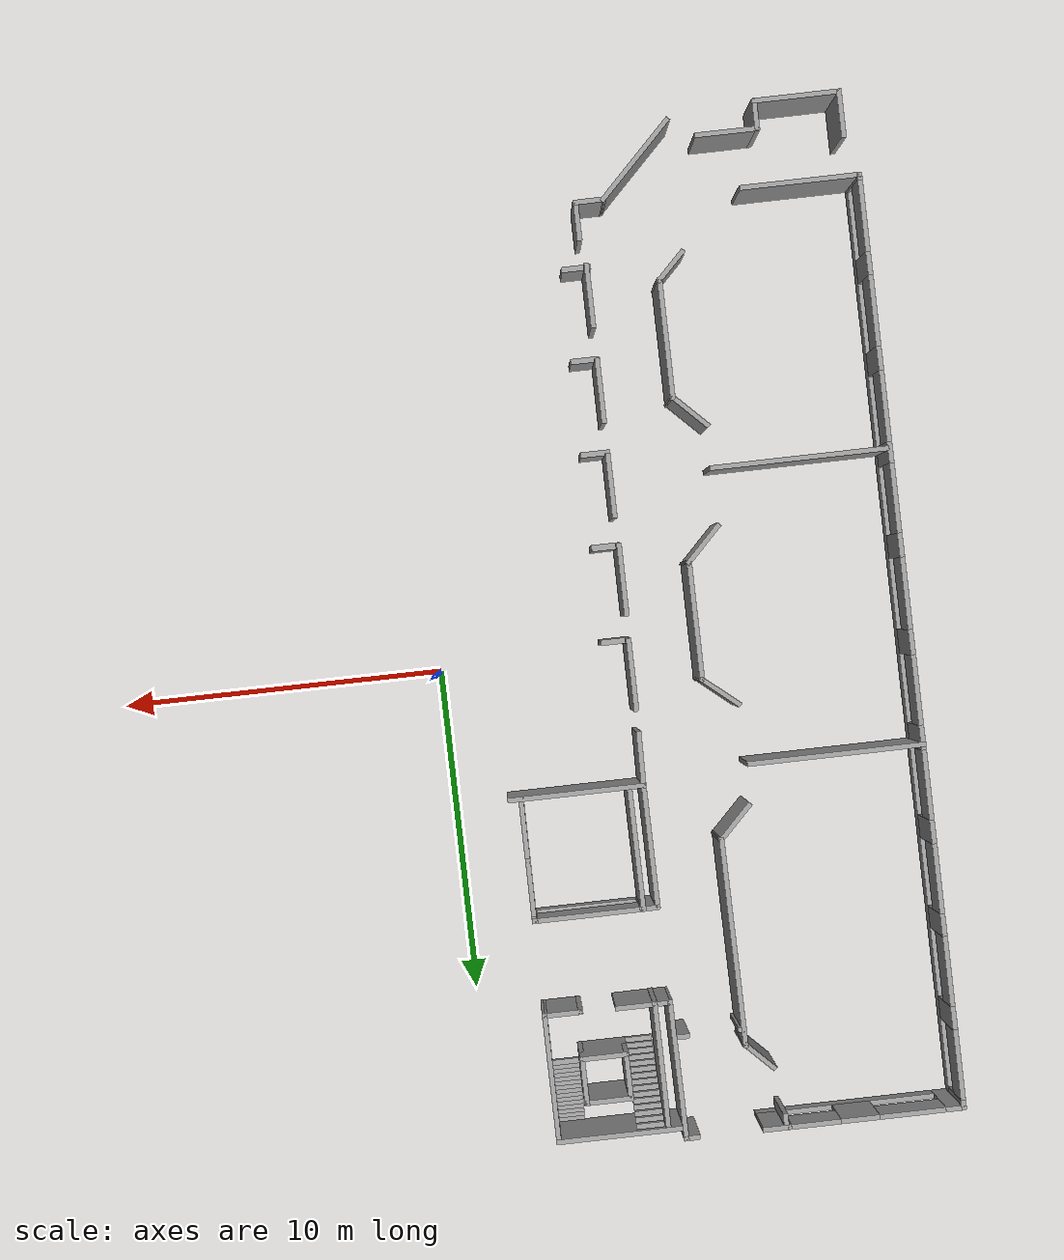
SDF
<?xml version='1.0'?>
<sdf version='1.6'>
  <model name='ca_vignal_1'>
    <pose frame=''>-8.09627 -0.676503 0 0 -0 0</pose>
    <link name='Door_0'>
      <collision name='Door_0_Collision'>
        <geometry>
          <box>
            <size>0.865695 0.2 2</size>
          </box>
        </geometry>
        <pose frame=''>0 0 1 0 -0 0</pose>
      </collision>
      <visual name='Door_0_Visual'>
        <pose frame=''>0 0 1 0 -0 0</pose>
        <geometry>
          <box>
            <size>0.865695 0.2 2</size>
          </box>
        </geometry>
        <material>
          <script>
            <uri>file://media/materials/scripts/gazebo.material</uri>
            <name>Gazebo/Grey</name>
          </script>
        </material>
      </visual>
      <pose frame=''>2.58868 -2.60647 0 0 -0 0</pose>
    </link>
    <link name='Door_1'>
      <collision name='Door_1_Collision'>
        <geometry>
          <box>
            <size>0.9 0.17 2</size>
          </box>
        </geometry>
        <pose frame=''>0 0 1 0 -0 0</pose>
      </collision>
      <visual name='Door_1_Visual'>
        <pose frame=''>0 0 1 0 -0 0</pose>
        <geometry>
          <box>
            <size>0.9 0.17 2</size>
          </box>
        </geometry>
        <material>
          <script>
            <uri>file://media/materials/scripts/gazebo.material</uri>
            <name>Gazebo/Grey</name>
          </script>
        </material>
      </visual>
      <pose frame=''>2.62198 0.308665 0 0 -0 0</pose>
    </link>
    <link name='Door_2'>
      <collision name='Door_2_Collision'>
        <geometry>
          <box>
            <size>0.9 0.17 2</size>
          </box>
        </geometry>
        <pose frame=''>0 0 1 0 -0 0</pose>
      </collision>
      <visual name='Door_2_Visual'>
        <pose frame=''>0 0 1 0 -0 0</pose>
        <geometry>
          <box>
            <size>0.9 0.17 2</size>
          </box>
        </geometry>
        <material>
          <script>
            <uri>file://media/materials/scripts/gazebo.material</uri>
            <name>Gazebo/Grey</name>
          </script>
        </material>
      </visual>
      <pose frame=''>2.58767 -5.48891 0 0 -0 0</pose>
    </link>
    <link name='Door_3'>
      <collision name='Door_3_Collision'>
        <geometry>
          <box>
            <size>0.9 0.17 2</size>
          </box>
        </geometry>
        <pose frame=''>0 0 1 0 -0 0</pose>
      </collision>
      <visual name='Door_3_Visual'>
        <pose frame=''>0 0 1 0 -0 0</pose>
        <geometry>
          <box>
            <size>0.9 0.17 2</size>
          </box>
        </geometry>
        <material>
          <script>
            <uri>file://media/materials/scripts/gazebo.material</uri>
            <name>Gazebo/Grey</name>
          </script>
        </material>
      </visual>
      <pose frame=''>2.57631 -8.37477 0 0 -0 0</pose>
    </link>
    <link name='Door_4'>
      <collision name='Door_4_Collision'>
        <geometry>
          <box>
            <size>0.9 0.17 2</size>
          </box>
        </geometry>
        <pose frame=''>0 0 1 0 -0 0</pose>
      </collision>
      <visual name='Door_4_Visual'>
        <pose frame=''>0 0 1 0 -0 0</pose>
        <geometry>
          <box>
            <size>0.9 0.17 2</size>
          </box>
        </geometry>
        <material>
          <script>
            <uri>file://media/materials/scripts/gazebo.material</uri>
            <name>Gazebo/Grey</name>
          </script>
        </material>
      </visual>
      <pose frame=''>2.53686 -11.2152 0 0 -0 0</pose>
    </link>
    <link name='Stairs_0'>
      <visual name='Stairs_0_Visual_0'>
        <pose frame=''>5.56857 15.1204 0.083333 0 -0 0</pose>
        <geometry>
          <box>
            <size>0.816 0.160476 0.166667</size>
          </box>
        </geometry>
        <material>
          <script>
            <uri>file://media/materials/scripts/gazebo.material</uri>
            <name>Gazebo/Grey</name>
          </script>
          <ambient>1 1 1 1</ambient>
        </material>
      </visual>
      <collision name='Stairs_0_Collision_0'>
        <geometry>
          <box>
            <size>0.816 0.160476 0.166667</size>
          </box>
        </geometry>
        <pose frame=''>5.56857 15.1204 0.083333 0 -0 0</pose>
      </collision>
      <visual name='Stairs_0_Visual_1'>
        <pose frame=''>5.56857 14.96 0.25 0 -0 0</pose>
        <geometry>
          <box>
            <size>0.816 0.160476 0.166667</size>
          </box>
        </geometry>
        <material>
          <script>
            <uri>file://media/materials/scripts/gazebo.material</uri>
            <name>Gazebo/Grey</name>
          </script>
          <ambient>1 1 1 1</ambient>
        </material>
      </visual>
      <collision name='Stairs_0_Collision_1'>
        <geometry>
          <box>
            <size>0.816 0.160476 0.166667</size>
          </box>
        </geometry>
        <pose frame=''>5.56857 14.96 0.25 0 -0 0</pose>
      </collision>
      <visual name='Stairs_0_Visual_2'>
        <pose frame=''>5.56857 14.7995 0.416667 0 -0 0</pose>
        <geometry>
          <box>
            <size>0.816 0.160476 0.166667</size>
          </box>
        </geometry>
        <material>
          <script>
            <uri>file://media/materials/scripts/gazebo.material</uri>
            <name>Gazebo/Grey</name>
          </script>
          <ambient>1 1 1 1</ambient>
        </material>
      </visual>
      <collision name='Stairs_0_Collision_2'>
        <geometry>
          <box>
            <size>0.816 0.160476 0.166667</size>
          </box>
        </geometry>
        <pose frame=''>5.56857 14.7995 0.416667 0 -0 0</pose>
      </collision>
      <visual name='Stairs_0_Visual_3'>
        <pose frame=''>5.56857 14.639 0.583333 0 -0 0</pose>
        <geometry>
          <box>
            <size>0.816 0.160476 0.166667</size>
          </box>
        </geometry>
        <material>
          <script>
            <uri>file://media/materials/scripts/gazebo.material</uri>
            <name>Gazebo/Grey</name>
          </script>
          <ambient>1 1 1 1</ambient>
        </material>
      </visual>
      <collision name='Stairs_0_Collision_3'>
        <geometry>
          <box>
            <size>0.816 0.160476 0.166667</size>
          </box>
        </geometry>
        <pose frame=''>5.56857 14.639 0.583333 0 -0 0</pose>
      </collision>
      <visual name='Stairs_0_Visual_4'>
        <pose frame=''>5.56857 14.4785 0.75 0 -0 0</pose>
        <geometry>
          <box>
            <size>0.816 0.160476 0.166667</size>
          </box>
        </geometry>
        <material>
          <script>
            <uri>file://media/materials/scripts/gazebo.material</uri>
            <name>Gazebo/Grey</name>
          </script>
          <ambient>1 1 1 1</ambient>
        </material>
      </visual>
      <collision name='Stairs_0_Collision_4'>
        <geometry>
          <box>
            <size>0.816 0.160476 0.166667</size>
          </box>
        </geometry>
        <pose frame=''>5.56857 14.4785 0.75 0 -0 0</pose>
      </collision>
      <visual name='Stairs_0_Visual_5'>
        <pose frame=''>5.56857 14.3181 0.916667 0 -0 0</pose>
        <geometry>
          <box>
            <size>0.816 0.160476 0.166667</size>
          </box>
        </geometry>
        <material>
          <script>
            <uri>file://media/materials/scripts/gazebo.material</uri>
            <name>Gazebo/Grey</name>
          </script>
          <ambient>1 1 1 1</ambient>
        </material>
      </visual>
      <collision name='Stairs_0_Collision_5'>
        <geometry>
          <box>
            <size>0.816 0.160476 0.166667</size>
          </box>
        </geometry>
        <pose frame=''>5.56857 14.3181 0.916667 0 -0 0</pose>
      </collision>
      <visual name='Stairs_0_Visual_6'>
        <pose frame=''>5.56857 14.1576 1.08333 0 -0 0</pose>
        <geometry>
          <box>
            <size>0.816 0.160476 0.166667</size>
          </box>
        </geometry>
        <material>
          <script>
            <uri>file://media/materials/scripts/gazebo.material</uri>
            <name>Gazebo/Grey</name>
          </script>
          <ambient>1 1 1 1</ambient>
        </material>
      </visual>
      <collision name='Stairs_0_Collision_6'>
        <geometry>
          <box>
            <size>0.816 0.160476 0.166667</size>
          </box>
        </geometry>
        <pose frame=''>5.56857 14.1576 1.08333 0 -0 0</pose>
      </collision>
      <visual name='Stairs_0_Visual_7'>
        <pose frame=''>5.56857 13.9971 1.25 0 -0 0</pose>
        <geometry>
          <box>
            <size>0.816 0.160476 0.166667</size>
          </box>
        </geometry>
        <material>
          <script>
            <uri>file://media/materials/scripts/gazebo.material</uri>
            <name>Gazebo/Grey</name>
          </script>
          <ambient>1 1 1 1</ambient>
        </material>
      </visual>
      <collision name='Stairs_0_Collision_7'>
        <geometry>
          <box>
            <size>0.816 0.160476 0.166667</size>
          </box>
        </geometry>
        <pose frame=''>5.56857 13.9971 1.25 0 -0 0</pose>
      </collision>
      <visual name='Stairs_0_Visual_8'>
        <pose frame=''>5.56857 13.8366 1.41667 0 -0 0</pose>
        <geometry>
          <box>
            <size>0.816 0.160476 0.166667</size>
          </box>
        </geometry>
        <material>
          <script>
            <uri>file://media/materials/scripts/gazebo.material</uri>
            <name>Gazebo/Grey</name>
          </script>
          <ambient>1 1 1 1</ambient>
        </material>
      </visual>
      <collision name='Stairs_0_Collision_8'>
        <geometry>
          <box>
            <size>0.816 0.160476 0.166667</size>
          </box>
        </geometry>
        <pose frame=''>5.56857 13.8366 1.41667 0 -0 0</pose>
      </collision>
      <visual name='Stairs_0_Visual_9'>
        <pose frame=''>5.56857 13.6762 1.58333 0 -0 0</pose>
        <geometry>
          <box>
            <size>0.816 0.160476 0.166667</size>
          </box>
        </geometry>
        <material>
          <script>
            <uri>file://media/materials/scripts/gazebo.material</uri>
            <name>Gazebo/Grey</name>
          </script>
          <ambient>1 1 1 1</ambient>
        </material>
      </visual>
      <collision name='Stairs_0_Collision_9'>
        <geometry>
          <box>
            <size>0.816 0.160476 0.166667</size>
          </box>
        </geometry>
        <pose frame=''>5.56857 13.6762 1.58333 0 -0 0</pose>
      </collision>
      <visual name='Stairs_0_Visual_10'>
        <pose frame=''>5.56857 13.5157 1.75 0 -0 0</pose>
        <geometry>
          <box>
            <size>0.816 0.160476 0.166667</size>
          </box>
        </geometry>
        <material>
          <script>
            <uri>file://media/materials/scripts/gazebo.material</uri>
            <name>Gazebo/Grey</name>
          </script>
          <ambient>1 1 1 1</ambient>
        </material>
      </visual>
      <collision name='Stairs_0_Collision_10'>
        <geometry>
          <box>
            <size>0.816 0.160476 0.166667</size>
          </box>
        </geometry>
        <pose frame=''>5.56857 13.5157 1.75 0 -0 0</pose>
      </collision>
      <visual name='Stairs_0_Visual_11'>
        <pose frame=''>5.56857 13.3552 1.91667 0 -0 0</pose>
        <geometry>
          <box>
            <size>0.816 0.160476 0.166667</size>
          </box>
        </geometry>
        <material>
          <script>
            <uri>file://media/materials/scripts/gazebo.material</uri>
            <name>Gazebo/Grey</name>
          </script>
          <ambient>1 1 1 1</ambient>
        </material>
      </visual>
      <collision name='Stairs_0_Collision_11'>
        <geometry>
          <box>
            <size>0.816 0.160476 0.166667</size>
          </box>
        </geometry>
        <pose frame=''>5.56857 13.3552 1.91667 0 -0 0</pose>
      </collision>
      <visual name='Stairs_0_Visual_12'>
        <pose frame=''>5.56857 13.1947 2.08333 0 -0 0</pose>
        <geometry>
          <box>
            <size>0.816 0.160476 0.166667</size>
          </box>
        </geometry>
        <material>
          <script>
            <uri>file://media/materials/scripts/gazebo.material</uri>
            <name>Gazebo/Grey</name>
          </script>
          <ambient>1 1 1 1</ambient>
        </material>
      </visual>
      <collision name='Stairs_0_Collision_12'>
        <geometry>
          <box>
            <size>0.816 0.160476 0.166667</size>
          </box>
        </geometry>
        <pose frame=''>5.56857 13.1947 2.08333 0 -0 0</pose>
      </collision>
      <visual name='Stairs_0_Visual_13'>
        <pose frame=''>5.56857 13.0343 2.25 0 -0 0</pose>
        <geometry>
          <box>
            <size>0.816 0.160476 0.166667</size>
          </box>
        </geometry>
        <material>
          <script>
            <uri>file://media/materials/scripts/gazebo.material</uri>
            <name>Gazebo/Grey</name>
          </script>
          <ambient>1 1 1 1</ambient>
        </material>
      </visual>
      <collision name='Stairs_0_Collision_13'>
        <geometry>
          <box>
            <size>0.816 0.160476 0.166667</size>
          </box>
        </geometry>
        <pose frame=''>5.56857 13.0343 2.25 0 -0 0</pose>
      </collision>
      <visual name='Stairs_0_Visual_14'>
        <pose frame=''>5.56857 12.8738 2.41667 0 -0 0</pose>
        <geometry>
          <box>
            <size>0.816 0.160476 0.166667</size>
          </box>
        </geometry>
        <material>
          <script>
            <uri>file://media/materials/scripts/gazebo.material</uri>
            <name>Gazebo/Grey</name>
          </script>
          <ambient>1 1 1 1</ambient>
        </material>
      </visual>
      <collision name='Stairs_0_Collision_14'>
        <geometry>
          <box>
            <size>0.816 0.160476 0.166667</size>
          </box>
        </geometry>
        <pose frame=''>5.56857 12.8738 2.41667 0 -0 0</pose>
      </collision>
    </link>
    <link name='Stairs_1'>
      <visual name='Stairs_1_Visual_0'>
        <pose frame=''>3.21816 12.8727 0.083333 0 -0 -3.14159</pose>
        <geometry>
          <box>
            <size>0.849625 0.158942 0.166667</size>
          </box>
        </geometry>
        <material>
          <script>
            <uri>file://media/materials/scripts/gazebo.material</uri>
            <name>Gazebo/Grey</name>
          </script>
          <ambient>1 1 1 1</ambient>
        </material>
      </visual>
      <collision name='Stairs_1_Collision_0'>
        <geometry>
          <box>
            <size>0.849625 0.158942 0.166667</size>
          </box>
        </geometry>
        <pose frame=''>3.21816 12.8727 0.083333 0 -0 -3.14159</pose>
      </collision>
      <visual name='Stairs_1_Visual_1'>
        <pose frame=''>3.21816 13.0316 0.25 0 -0 -3.14159</pose>
        <geometry>
          <box>
            <size>0.849625 0.158942 0.166667</size>
          </box>
        </geometry>
        <material>
          <script>
            <uri>file://media/materials/scripts/gazebo.material</uri>
            <name>Gazebo/Grey</name>
          </script>
          <ambient>1 1 1 1</ambient>
        </material>
      </visual>
      <collision name='Stairs_1_Collision_1'>
        <geometry>
          <box>
            <size>0.849625 0.158942 0.166667</size>
          </box>
        </geometry>
        <pose frame=''>3.21816 13.0316 0.25 0 -0 -3.14159</pose>
      </collision>
      <visual name='Stairs_1_Visual_2'>
        <pose frame=''>3.21816 13.1906 0.416667 0 -0 -3.14159</pose>
        <geometry>
          <box>
            <size>0.849625 0.158942 0.166667</size>
          </box>
        </geometry>
        <material>
          <script>
            <uri>file://media/materials/scripts/gazebo.material</uri>
            <name>Gazebo/Grey</name>
          </script>
          <ambient>1 1 1 1</ambient>
        </material>
      </visual>
      <collision name='Stairs_1_Collision_2'>
        <geometry>
          <box>
            <size>0.849625 0.158942 0.166667</size>
          </box>
        </geometry>
        <pose frame=''>3.21816 13.1906 0.416667 0 -0 -3.14159</pose>
      </collision>
      <visual name='Stairs_1_Visual_3'>
        <pose frame=''>3.21816 13.3495 0.583333 0 -0 -3.14159</pose>
        <geometry>
          <box>
            <size>0.849625 0.158942 0.166667</size>
          </box>
        </geometry>
        <material>
          <script>
            <uri>file://media/materials/scripts/gazebo.material</uri>
            <name>Gazebo/Grey</name>
          </script>
          <ambient>1 1 1 1</ambient>
        </material>
      </visual>
      <collision name='Stairs_1_Collision_3'>
        <geometry>
          <box>
            <size>0.849625 0.158942 0.166667</size>
          </box>
        </geometry>
        <pose frame=''>3.21816 13.3495 0.583333 0 -0 -3.14159</pose>
      </collision>
      <visual name='Stairs_1_Visual_4'>
        <pose frame=''>3.21816 13.5085 0.75 0 -0 -3.14159</pose>
        <geometry>
          <box>
            <size>0.849625 0.158942 0.166667</size>
          </box>
        </geometry>
        <material>
          <script>
            <uri>file://media/materials/scripts/gazebo.material</uri>
            <name>Gazebo/Grey</name>
          </script>
          <ambient>1 1 1 1</ambient>
        </material>
      </visual>
      <collision name='Stairs_1_Collision_4'>
        <geometry>
          <box>
            <size>0.849625 0.158942 0.166667</size>
          </box>
        </geometry>
        <pose frame=''>3.21816 13.5085 0.75 0 -0 -3.14159</pose>
      </collision>
      <visual name='Stairs_1_Visual_5'>
        <pose frame=''>3.21816 13.6674 0.916667 0 -0 -3.14159</pose>
        <geometry>
          <box>
            <size>0.849625 0.158942 0.166667</size>
          </box>
        </geometry>
        <material>
          <script>
            <uri>file://media/materials/scripts/gazebo.material</uri>
            <name>Gazebo/Grey</name>
          </script>
          <ambient>1 1 1 1</ambient>
        </material>
      </visual>
      <collision name='Stairs_1_Collision_5'>
        <geometry>
          <box>
            <size>0.849625 0.158942 0.166667</size>
          </box>
        </geometry>
        <pose frame=''>3.21816 13.6674 0.916667 0 -0 -3.14159</pose>
      </collision>
      <visual name='Stairs_1_Visual_6'>
        <pose frame=''>3.21816 13.8263 1.08333 0 -0 -3.14159</pose>
        <geometry>
          <box>
            <size>0.849625 0.158942 0.166667</size>
          </box>
        </geometry>
        <material>
          <script>
            <uri>file://media/materials/scripts/gazebo.material</uri>
            <name>Gazebo/Grey</name>
          </script>
          <ambient>1 1 1 1</ambient>
        </material>
      </visual>
      <collision name='Stairs_1_Collision_6'>
        <geometry>
          <box>
            <size>0.849625 0.158942 0.166667</size>
          </box>
        </geometry>
        <pose frame=''>3.21816 13.8263 1.08333 0 -0 -3.14159</pose>
      </collision>
      <visual name='Stairs_1_Visual_7'>
        <pose frame=''>3.21816 13.9853 1.25 0 -0 -3.14159</pose>
        <geometry>
          <box>
            <size>0.849625 0.158942 0.166667</size>
          </box>
        </geometry>
        <material>
          <script>
            <uri>file://media/materials/scripts/gazebo.material</uri>
            <name>Gazebo/Grey</name>
          </script>
          <ambient>1 1 1 1</ambient>
        </material>
      </visual>
      <collision name='Stairs_1_Collision_7'>
        <geometry>
          <box>
            <size>0.849625 0.158942 0.166667</size>
          </box>
        </geometry>
        <pose frame=''>3.21816 13.9853 1.25 0 -0 -3.14159</pose>
      </collision>
      <visual name='Stairs_1_Visual_8'>
        <pose frame=''>3.21816 14.1442 1.41667 0 -0 -3.14159</pose>
        <geometry>
          <box>
            <size>0.849625 0.158942 0.166667</size>
          </box>
        </geometry>
        <material>
          <script>
            <uri>file://media/materials/scripts/gazebo.material</uri>
            <name>Gazebo/Grey</name>
          </script>
          <ambient>1 1 1 1</ambient>
        </material>
      </visual>
      <collision name='Stairs_1_Collision_8'>
        <geometry>
          <box>
            <size>0.849625 0.158942 0.166667</size>
          </box>
        </geometry>
        <pose frame=''>3.21816 14.1442 1.41667 0 -0 -3.14159</pose>
      </collision>
      <visual name='Stairs_1_Visual_9'>
        <pose frame=''>3.21816 14.3032 1.58333 0 -0 -3.14159</pose>
        <geometry>
          <box>
            <size>0.849625 0.158942 0.166667</size>
          </box>
        </geometry>
        <material>
          <script>
            <uri>file://media/materials/scripts/gazebo.material</uri>
            <name>Gazebo/Grey</name>
          </script>
          <ambient>1 1 1 1</ambient>
        </material>
      </visual>
      <collision name='Stairs_1_Collision_9'>
        <geometry>
          <box>
            <size>0.849625 0.158942 0.166667</size>
          </box>
        </geometry>
        <pose frame=''>3.21816 14.3032 1.58333 0 -0 -3.14159</pose>
      </collision>
      <visual name='Stairs_1_Visual_10'>
        <pose frame=''>3.21816 14.4621 1.75 0 -0 -3.14159</pose>
        <geometry>
          <box>
            <size>0.849625 0.158942 0.166667</size>
          </box>
        </geometry>
        <material>
          <script>
            <uri>file://media/materials/scripts/gazebo.material</uri>
            <name>Gazebo/Grey</name>
          </script>
          <ambient>1 1 1 1</ambient>
        </material>
      </visual>
      <collision name='Stairs_1_Collision_10'>
        <geometry>
          <box>
            <size>0.849625 0.158942 0.166667</size>
          </box>
        </geometry>
        <pose frame=''>3.21816 14.4621 1.75 0 -0 -3.14159</pose>
      </collision>
      <visual name='Stairs_1_Visual_11'>
        <pose frame=''>3.21816 14.6211 1.91667 0 -0 -3.14159</pose>
        <geometry>
          <box>
            <size>0.849625 0.158942 0.166667</size>
          </box>
        </geometry>
        <material>
          <script>
            <uri>file://media/materials/scripts/gazebo.material</uri>
            <name>Gazebo/Grey</name>
          </script>
          <ambient>1 1 1 1</ambient>
        </material>
      </visual>
      <collision name='Stairs_1_Collision_11'>
        <geometry>
          <box>
            <size>0.849625 0.158942 0.166667</size>
          </box>
        </geometry>
        <pose frame=''>3.21816 14.6211 1.91667 0 -0 -3.14159</pose>
      </collision>
      <visual name='Stairs_1_Visual_12'>
        <pose frame=''>3.21816 14.78 2.08333 0 -0 -3.14159</pose>
        <geometry>
          <box>
            <size>0.849625 0.158942 0.166667</size>
          </box>
        </geometry>
        <material>
          <script>
            <uri>file://media/materials/scripts/gazebo.material</uri>
            <name>Gazebo/Grey</name>
          </script>
          <ambient>1 1 1 1</ambient>
        </material>
      </visual>
      <collision name='Stairs_1_Collision_12'>
        <geometry>
          <box>
            <size>0.849625 0.158942 0.166667</size>
          </box>
        </geometry>
        <pose frame=''>3.21816 14.78 2.08333 0 -0 -3.14159</pose>
      </collision>
      <visual name='Stairs_1_Visual_13'>
        <pose frame=''>3.21816 14.9389 2.25 0 -0 -3.14159</pose>
        <geometry>
          <box>
            <size>0.849625 0.158942 0.166667</size>
          </box>
        </geometry>
        <material>
          <script>
            <uri>file://media/materials/scripts/gazebo.material</uri>
            <name>Gazebo/Grey</name>
          </script>
          <ambient>1 1 1 1</ambient>
        </material>
      </visual>
      <collision name='Stairs_1_Collision_13'>
        <geometry>
          <box>
            <size>0.849625 0.158942 0.166667</size>
          </box>
        </geometry>
        <pose frame=''>3.21816 14.9389 2.25 0 -0 -3.14159</pose>
      </collision>
      <visual name='Stairs_1_Visual_14'>
        <pose frame=''>3.21816 15.0979 2.41667 0 -0 -3.14159</pose>
        <geometry>
          <box>
            <size>0.849625 0.158942 0.166667</size>
          </box>
        </geometry>
        <material>
          <script>
            <uri>file://media/materials/scripts/gazebo.material</uri>
            <name>Gazebo/Grey</name>
          </script>
          <ambient>1 1 1 1</ambient>
        </material>
      </visual>
      <collision name='Stairs_1_Collision_14'>
        <geometry>
          <box>
            <size>0.849625 0.158942 0.166667</size>
          </box>
        </geometry>
        <pose frame=''>3.21816 15.0979 2.41667 0 -0 -3.14159</pose>
      </collision>
    </link>
    <link name='Wall_0'>
      <pose frame=''>-6.35164 1.29841 0 0 -0 1.5708</pose>
      <visual name='Wall_0_Visual_0'>
        <pose frame=''>-14.2835 0 1.25 0 -0 0</pose>
        <geometry>
          <box>
            <size>0.235089 0.15 2.5</size>
          </box>
        </geometry>
        <material>
          <script>
            <uri>file://media/materials/scripts/gazebo.material</uri>
            <name>Gazebo/Grey</name>
          </script>
          <ambient>1 1 1 1</ambient>
        </material>
      </visual>
      <collision name='Wall_0_Collision_0'>
        <geometry>
          <box>
            <size>0.235089 0.15 2.5</size>
          </box>
        </geometry>
        <pose frame=''>-14.2835 0 1.25 0 -0 0</pose>
      </collision>
      <visual name='Wall_0_Visual_1'>
        <pose frame=''>0.117544 0 0.25 0 -0 0</pose>
        <geometry>
          <box>
            <size>28.5671 0.15 0.5</size>
          </box>
        </geometry>
        <material>
          <script>
            <uri>file://media/materials/scripts/gazebo.material</uri>
            <name>Gazebo/Grey</name>
          </script>
          <ambient>1 1 1 1</ambient>
        </material>
      </visual>
      <collision name='Wall_0_Collision_1'>
        <geometry>
          <box>
            <size>28.5671 0.15 0.5</size>
          </box>
        </geometry>
        <pose frame=''>0.117544 0 0.25 0 -0 0</pose>
      </collision>
      <visual name='Wall_0_Visual_2'>
        <pose frame=''>-11.5998 0 1.5 0 -0 0</pose>
        <geometry>
          <box>
            <size>0.716549 0.15 2</size>
          </box>
        </geometry>
        <material>
          <script>
            <uri>file://media/materials/scripts/gazebo.material</uri>
            <name>Gazebo/Grey</name>
          </script>
          <ambient>1 1 1 1</ambient>
        </material>
      </visual>
      <collision name='Wall_0_Collision_2'>
        <geometry>
          <box>
            <size>0.716549 0.15 2</size>
          </box>
        </geometry>
        <pose frame=''>-11.5998 0 1.5 0 -0 0</pose>
      </collision>
      <visual name='Wall_0_Visual_3'>
        <pose frame=''>-8.68449 0 1.5 0 -0 0</pose>
        <geometry>
          <box>
            <size>0.738343 0.15 2</size>
          </box>
        </geometry>
        <material>
          <script>
            <uri>file://media/materials/scripts/gazebo.material</uri>
            <name>Gazebo/Grey</name>
          </script>
          <ambient>1 1 1 1</ambient>
        </material>
      </visual>
      <collision name='Wall_0_Collision_3'>
        <geometry>
          <box>
            <size>0.738343 0.15 2</size>
          </box>
        </geometry>
        <pose frame=''>-8.68449 0 1.5 0 -0 0</pose>
      </collision>
      <visual name='Wall_0_Visual_4'>
        <pose frame=''>-5.79269 0 1.5 0 -0 0</pose>
        <geometry>
          <box>
            <size>0.646852 0.15 2</size>
          </box>
        </geometry>
        <material>
          <script>
            <uri>file://media/materials/scripts/gazebo.material</uri>
            <name>Gazebo/Grey</name>
          </script>
          <ambient>1 1 1 1</ambient>
        </material>
      </visual>
      <collision name='Wall_0_Collision_4'>
        <geometry>
          <box>
            <size>0.646852 0.15 2</size>
          </box>
        </geometry>
        <pose frame=''>-5.79269 0 1.5 0 -0 0</pose>
      </collision>
      <visual name='Wall_0_Visual_5'>
        <pose frame=''>-2.9503 0 1.5 0 -0 0</pose>
        <geometry>
          <box>
            <size>0.744454 0.15 2</size>
          </box>
        </geometry>
        <material>
          <script>
            <uri>file://media/materials/scripts/gazebo.material</uri>
            <name>Gazebo/Grey</name>
          </script>
          <ambient>1 1 1 1</ambient>
        </material>
      </visual>
      <collision name='Wall_0_Collision_5'>
        <geometry>
          <box>
            <size>0.744454 0.15 2</size>
          </box>
        </geometry>
        <pose frame=''>-2.9503 0 1.5 0 -0 0</pose>
      </collision>
      <visual name='Wall_0_Visual_6'>
        <pose frame=''>0.028378 0 1.5 0 -0 0</pose>
        <geometry>
          <box>
            <size>0.779514 0.15 2</size>
          </box>
        </geometry>
        <material>
          <script>
            <uri>file://media/materials/scripts/gazebo.material</uri>
            <name>Gazebo/Grey</name>
          </script>
          <ambient>1 1 1 1</ambient>
        </material>
      </visual>
      <collision name='Wall_0_Collision_6'>
        <geometry>
          <box>
            <size>0.779514 0.15 2</size>
          </box>
        </geometry>
        <pose frame=''>0.028378 0 1.5 0 -0 0</pose>
      </collision>
      <visual name='Wall_0_Visual_7'>
        <pose frame=''>2.96332 0 1.5 0 -0 0</pose>
        <geometry>
          <box>
            <size>0.761928 0.15 2</size>
          </box>
        </geometry>
        <material>
          <script>
            <uri>file://media/materials/scripts/gazebo.material</uri>
            <name>Gazebo/Grey</name>
          </script>
          <ambient>1 1 1 1</ambient>
        </material>
      </visual>
      <collision name='Wall_0_Collision_7'>
        <geometry>
          <box>
            <size>0.761928 0.15 2</size>
          </box>
        </geometry>
        <pose frame=''>2.96332 0 1.5 0 -0 0</pose>
      </collision>
      <visual name='Wall_0_Visual_8'>
        <pose frame=''>5.85759 0 1.5 0 -0 0</pose>
        <geometry>
          <box>
            <size>0.733132 0.15 2</size>
          </box>
        </geometry>
        <material>
          <script>
            <uri>file://media/materials/scripts/gazebo.material</uri>
            <name>Gazebo/Grey</name>
          </script>
          <ambient>1 1 1 1</ambient>
        </material>
      </visual>
      <collision name='Wall_0_Collision_8'>
        <geometry>
          <box>
            <size>0.733132 0.15 2</size>
          </box>
        </geometry>
        <pose frame=''>5.85759 0 1.5 0 -0 0</pose>
      </collision>
      <visual name='Wall_0_Visual_9'>
        <pose frame=''>8.71919 0 1.5 0 -0 0</pose>
        <geometry>
          <box>
            <size>0.696864 0.15 2</size>
          </box>
        </geometry>
        <material>
          <script>
            <uri>file://media/materials/scripts/gazebo.material</uri>
            <name>Gazebo/Grey</name>
          </script>
          <ambient>1 1 1 1</ambient>
        </material>
      </visual>
      <collision name='Wall_0_Collision_9'>
        <geometry>
          <box>
            <size>0.696864 0.15 2</size>
          </box>
        </geometry>
        <pose frame=''>8.71919 0 1.5 0 -0 0</pose>
      </collision>
      <visual name='Wall_0_Visual_10'>
        <pose frame=''>11.5805 0 1.5 0 -0 0</pose>
        <geometry>
          <box>
            <size>0.718517 0.15 2</size>
          </box>
        </geometry>
        <material>
          <script>
            <uri>file://media/materials/scripts/gazebo.material</uri>
            <name>Gazebo/Grey</name>
          </script>
          <ambient>1 1 1 1</ambient>
        </material>
      </visual>
      <collision name='Wall_0_Collision_10'>
        <geometry>
          <box>
            <size>0.718517 0.15 2</size>
          </box>
        </geometry>
        <pose frame=''>11.5805 0 1.5 0 -0 0</pose>
      </collision>
      <visual name='Wall_0_Visual_11'>
        <pose frame=''>14.2472 0 1.5 0 -0 0</pose>
        <geometry>
          <box>
            <size>0.30779 0.15 2</size>
          </box>
        </geometry>
        <material>
          <script>
            <uri>file://media/materials/scripts/gazebo.material</uri>
            <name>Gazebo/Grey</name>
          </script>
          <ambient>1 1 1 1</ambient>
        </material>
      </visual>
      <collision name='Wall_0_Collision_11'>
        <geometry>
          <box>
            <size>0.30779 0.15 2</size>
          </box>
        </geometry>
        <pose frame=''>14.2472 0 1.5 0 -0 0</pose>
      </collision>
      <visual name='Wall_0_Visual_12'>
        <pose frame=''>-13.062 0 1.9 0 -0 0</pose>
        <geometry>
          <box>
            <size>2.20795 0.15 1.2</size>
          </box>
        </geometry>
        <material>
          <script>
            <uri>file://media/materials/scripts/gazebo.material</uri>
            <name>Gazebo/Grey</name>
          </script>
          <ambient>1 1 1 1</ambient>
        </material>
      </visual>
      <collision name='Wall_0_Collision_12'>
        <geometry>
          <box>
            <size>2.20795 0.15 1.2</size>
          </box>
        </geometry>
        <pose frame=''>-13.062 0 1.9 0 -0 0</pose>
      </collision>
      <visual name='Wall_0_Visual_13'>
        <pose frame=''>-10.1476 0 1.9 0 -0 0</pose>
        <geometry>
          <box>
            <size>2.18784 0.15 1.2</size>
          </box>
        </geometry>
        <material>
          <script>
            <uri>file://media/materials/scripts/gazebo.material</uri>
            <name>Gazebo/Grey</name>
          </script>
          <ambient>1 1 1 1</ambient>
        </material>
      </visual>
      <collision name='Wall_0_Collision_13'>
        <geometry>
          <box>
            <size>2.18784 0.15 1.2</size>
          </box>
        </geometry>
        <pose frame=''>-10.1476 0 1.9 0 -0 0</pose>
      </collision>
      <visual name='Wall_0_Visual_14'>
        <pose frame=''>-7.21572 0 1.9 0 -0 0</pose>
        <geometry>
          <box>
            <size>2.19921 0.15 1.2</size>
          </box>
        </geometry>
        <material>
          <script>
            <uri>file://media/materials/scripts/gazebo.material</uri>
            <name>Gazebo/Grey</name>
          </script>
          <ambient>1 1 1 1</ambient>
        </material>
      </visual>
      <collision name='Wall_0_Collision_14'>
        <geometry>
          <box>
            <size>2.19921 0.15 1.2</size>
          </box>
        </geometry>
        <pose frame=''>-7.21572 0 1.9 0 -0 0</pose>
      </collision>
      <visual name='Wall_0_Visual_15'>
        <pose frame=''>-4.3959 0 1.9 0 -0 0</pose>
        <geometry>
          <box>
            <size>2.14674 0.15 1.2</size>
          </box>
        </geometry>
        <material>
          <script>
            <uri>file://media/materials/scripts/gazebo.material</uri>
            <name>Gazebo/Grey</name>
          </script>
          <ambient>1 1 1 1</ambient>
        </material>
      </visual>
      <collision name='Wall_0_Collision_15'>
        <geometry>
          <box>
            <size>2.14674 0.15 1.2</size>
          </box>
        </geometry>
        <pose frame=''>-4.3959 0 1.9 0 -0 0</pose>
      </collision>
      <visual name='Wall_0_Visual_16'>
        <pose frame=''>-1.46973 0 1.9 0 -0 0</pose>
        <geometry>
          <box>
            <size>2.2167 0.15 1.2</size>
          </box>
        </geometry>
        <material>
          <script>
            <uri>file://media/materials/scripts/gazebo.material</uri>
            <name>Gazebo/Grey</name>
          </script>
          <ambient>1 1 1 1</ambient>
        </material>
      </visual>
      <collision name='Wall_0_Collision_16'>
        <geometry>
          <box>
            <size>2.2167 0.15 1.2</size>
          </box>
        </geometry>
        <pose frame=''>-1.46973 0 1.9 0 -0 0</pose>
      </collision>
      <visual name='Wall_0_Visual_17'>
        <pose frame=''>1.50025 0 1.9 0 -0 0</pose>
        <geometry>
          <box>
            <size>2.16423 0.15 1.2</size>
          </box>
        </geometry>
        <material>
          <script>
            <uri>file://media/materials/scripts/gazebo.material</uri>
            <name>Gazebo/Grey</name>
          </script>
          <ambient>1 1 1 1</ambient>
        </material>
      </visual>
      <collision name='Wall_0_Collision_17'>
        <geometry>
          <box>
            <size>2.16423 0.15 1.2</size>
          </box>
        </geometry>
        <pose frame=''>1.50025 0 1.9 0 -0 0</pose>
      </collision>
      <visual name='Wall_0_Visual_18'>
        <pose frame=''>4.41765 0 1.9 0 -0 0</pose>
        <geometry>
          <box>
            <size>2.14674 0.15 1.2</size>
          </box>
        </geometry>
        <material>
          <script>
            <uri>file://media/materials/scripts/gazebo.material</uri>
            <name>Gazebo/Grey</name>
          </script>
          <ambient>1 1 1 1</ambient>
        </material>
      </visual>
      <collision name='Wall_0_Collision_18'>
        <geometry>
          <box>
            <size>2.14674 0.15 1.2</size>
          </box>
        </geometry>
        <pose frame=''>4.41765 0 1.9 0 -0 0</pose>
      </collision>
      <visual name='Wall_0_Visual_19'>
        <pose frame=''>7.29746 0 1.9 0 -0 0</pose>
        <geometry>
          <box>
            <size>2.1466 0.15 1.2</size>
          </box>
        </geometry>
        <material>
          <script>
            <uri>file://media/materials/scripts/gazebo.material</uri>
            <name>Gazebo/Grey</name>
          </script>
          <ambient>1 1 1 1</ambient>
        </material>
      </visual>
      <collision name='Wall_0_Collision_19'>
        <geometry>
          <box>
            <size>2.1466 0.15 1.2</size>
          </box>
        </geometry>
        <pose frame=''>7.29746 0 1.9 0 -0 0</pose>
      </collision>
      <visual name='Wall_0_Visual_20'>
        <pose frame=''>10.1444 0 1.9 0 -0 0</pose>
        <geometry>
          <box>
            <size>2.15358 0.15 1.2</size>
          </box>
        </geometry>
        <material>
          <script>
            <uri>file://media/materials/scripts/gazebo.material</uri>
            <name>Gazebo/Grey</name>
          </script>
          <ambient>1 1 1 1</ambient>
        </material>
      </visual>
      <collision name='Wall_0_Collision_20'>
        <geometry>
          <box>
            <size>2.15358 0.15 1.2</size>
          </box>
        </geometry>
        <pose frame=''>10.1444 0 1.9 0 -0 0</pose>
      </collision>
      <visual name='Wall_0_Visual_21'>
        <pose frame=''>13.0165 0 1.9 0 -0 0</pose>
        <geometry>
          <box>
            <size>2.15358 0.15 1.2</size>
          </box>
        </geometry>
        <material>
          <script>
            <uri>file://media/materials/scripts/gazebo.material</uri>
            <name>Gazebo/Grey</name>
          </script>
          <ambient>1 1 1 1</ambient>
        </material>
      </visual>
      <collision name='Wall_0_Collision_21'>
        <geometry>
          <box>
            <size>2.15358 0.15 1.2</size>
          </box>
        </geometry>
        <pose frame=''>13.0165 0 1.9 0 -0 0</pose>
      </collision>
    </link>
    <link name='Wall_10'>
      <collision name='Wall_10_Collision'>
        <geometry>
          <box>
            <size>1.49437 0.15 2.5</size>
          </box>
        </geometry>
        <pose frame=''>0 0 1.25 0 -0 0</pose>
      </collision>
      <visual name='Wall_10_Visual'>
        <pose frame=''>0 0 1.25 0 -0 0</pose>
        <geometry>
          <box>
            <size>1.49437 0.15 2.5</size>
          </box>
        </geometry>
        <material>
          <script>
            <uri>file://media/materials/scripts/gazebo.material</uri>
            <name>Gazebo/Grey</name>
          </script>
          <ambient>1 1 1 1</ambient>
        </material>
      </visual>
      <pose frame=''>-0.384063 2.18943 0 0 -0 2.44358</pose>
    </link>
    <link name='Wall_12'>
      <collision name='Wall_12_Collision'>
        <geometry>
          <box>
            <size>5.5 0.15 2.5</size>
          </box>
        </geometry>
        <pose frame=''>0 0 1.25 0 -0 0</pose>
      </collision>
      <visual name='Wall_12_Visual'>
        <pose frame=''>0 0 1.25 0 -0 0</pose>
        <geometry>
          <box>
            <size>5.5 0.15 2.5</size>
          </box>
        </geometry>
        <material>
          <script>
            <uri>file://media/materials/scripts/gazebo.material</uri>
            <name>Gazebo/Grey</name>
          </script>
          <ambient>1 1 1 1</ambient>
        </material>
      </visual>
      <pose frame=''>-3.57241 -4.63113 0 0 -0 0</pose>
    </link>
    <link name='Wall_14'>
      <collision name='Wall_14_Collision'>
        <geometry>
          <box>
            <size>3.75 0.15 2.5</size>
          </box>
        </geometry>
        <pose frame=''>0 0 1.25 0 -0 0</pose>
      </collision>
      <visual name='Wall_14_Visual'>
        <pose frame=''>0 0 1.25 0 -0 0</pose>
        <geometry>
          <box>
            <size>3.75 0.15 2.5</size>
          </box>
        </geometry>
        <material>
          <script>
            <uri>file://media/materials/scripts/gazebo.material</uri>
            <name>Gazebo/Grey</name>
          </script>
          <ambient>1 1 1 1</ambient>
        </material>
      </visual>
      <pose frame=''>-4.55164 -13.0277 0 0 -0 0</pose>
    </link>
    <link name='Wall_18'>
      <collision name='Wall_18_Collision'>
        <geometry>
          <box>
            <size>0.5 0.15 2.5</size>
          </box>
        </geometry>
        <pose frame=''>0 0 1.25 0 -0 0</pose>
      </collision>
      <visual name='Wall_18_Visual'>
        <pose frame=''>0 0 1.25 0 -0 0</pose>
        <geometry>
          <box>
            <size>0.5 0.15 2.5</size>
          </box>
        </geometry>
        <material>
          <script>
            <uri>file://media/materials/scripts/gazebo.material</uri>
            <name>Gazebo/Grey</name>
          </script>
          <ambient>1 1 1 1</ambient>
        </material>
      </visual>
      <pose frame=''>1.99078 15.6193 0 0 -0 0</pose>
    </link>
    <link name='Wall_19'>
      <collision name='Wall_19_Collision'>
        <geometry>
          <box>
            <size>4.33031 0.15 2.5</size>
          </box>
        </geometry>
        <pose frame=''>0 0 1.25 0 -0 0</pose>
      </collision>
      <visual name='Wall_19_Visual'>
        <pose frame=''>0 0 1.25 0 -0 0</pose>
        <geometry>
          <box>
            <size>4.33031 0.15 2.5</size>
          </box>
        </geometry>
        <material>
          <script>
            <uri>file://media/materials/scripts/gazebo.material</uri>
            <name>Gazebo/Grey</name>
          </script>
          <ambient>1 1 1 1</ambient>
        </material>
      </visual>
      <pose frame=''>2.1855 13.5292 0 0 0 -1.56136</pose>
    </link>
    <link name='Wall_2'>
      <pose frame=''>-3.30164 15.6245 0 0 -0 0</pose>
      <visual name='Wall_2_Visual_0'>
        <pose frame=''>-2.81084 0 1.25 0 -0 0</pose>
        <geometry>
          <box>
            <size>0.628319 0.15 2.5</size>
          </box>
        </geometry>
        <material>
          <script>
            <uri>file://media/materials/scripts/gazebo.material</uri>
            <name>Gazebo/Grey</name>
          </script>
          <ambient>1 1 1 1</ambient>
        </material>
      </visual>
      <collision name='Wall_2_Collision_0'>
        <geometry>
          <box>
            <size>0.628319 0.15 2.5</size>
          </box>
        </geometry>
        <pose frame=''>-2.81084 0 1.25 0 -0 0</pose>
      </collision>
      <visual name='Wall_2_Visual_1'>
        <pose frame=''>0.31416 0 0.25 0 -0 0</pose>
        <geometry>
          <box>
            <size>5.62168 0.15 0.5</size>
          </box>
        </geometry>
        <material>
          <script>
            <uri>file://media/materials/scripts/gazebo.material</uri>
            <name>Gazebo/Grey</name>
          </script>
          <ambient>1 1 1 1</ambient>
        </material>
      </visual>
      <collision name='Wall_2_Collision_1'>
        <geometry>
          <box>
            <size>5.62168 0.15 0.5</size>
          </box>
        </geometry>
        <pose frame=''>0.31416 0 0.25 0 -0 0</pose>
      </collision>
      <visual name='Wall_2_Visual_2'>
        <pose frame=''>0.127976 0 1.5 0 -0 0</pose>
        <geometry>
          <box>
            <size>1.18537 0.15 2</size>
          </box>
        </geometry>
        <material>
          <script>
            <uri>file://media/materials/scripts/gazebo.material</uri>
            <name>Gazebo/Grey</name>
          </script>
          <ambient>1 1 1 1</ambient>
        </material>
      </visual>
      <collision name='Wall_2_Collision_2'>
        <geometry>
          <box>
            <size>1.18537 0.15 2</size>
          </box>
        </geometry>
        <pose frame=''>0.127976 0 1.5 0 -0 0</pose>
      </collision>
      <visual name='Wall_2_Visual_3'>
        <pose frame=''>2.68462 0 1.5 0 -0 0</pose>
        <geometry>
          <box>
            <size>0.880764 0.15 2</size>
          </box>
        </geometry>
        <material>
          <script>
            <uri>file://media/materials/scripts/gazebo.material</uri>
            <name>Gazebo/Grey</name>
          </script>
          <ambient>1 1 1 1</ambient>
        </material>
      </visual>
      <collision name='Wall_2_Collision_3'>
        <geometry>
          <box>
            <size>0.880764 0.15 2</size>
          </box>
        </geometry>
        <pose frame=''>2.68462 0 1.5 0 -0 0</pose>
      </collision>
      <visual name='Wall_2_Visual_4'>
        <pose frame=''>-1.4807 0 1.9 0 -0 0</pose>
        <geometry>
          <box>
            <size>2.03197 0.15 1.2</size>
          </box>
        </geometry>
        <material>
          <script>
            <uri>file://media/materials/scripts/gazebo.material</uri>
            <name>Gazebo/Grey</name>
          </script>
          <ambient>1 1 1 1</ambient>
        </material>
      </visual>
      <collision name='Wall_2_Collision_4'>
        <geometry>
          <box>
            <size>2.03197 0.15 1.2</size>
          </box>
        </geometry>
        <pose frame=''>-1.4807 0 1.9 0 -0 0</pose>
      </collision>
      <visual name='Wall_2_Visual_5'>
        <pose frame=''>1.48245 0 1.9 0 -0 0</pose>
        <geometry>
          <box>
            <size>1.52357 0.15 1.2</size>
          </box>
        </geometry>
        <material>
          <script>
            <uri>file://media/materials/scripts/gazebo.material</uri>
            <name>Gazebo/Grey</name>
          </script>
          <ambient>1 1 1 1</ambient>
        </material>
      </visual>
      <collision name='Wall_2_Collision_5'>
        <geometry>
          <box>
            <size>1.52357 0.15 1.2</size>
          </box>
        </geometry>
        <pose frame=''>1.48245 0 1.9 0 -0 0</pose>
      </collision>
    </link>
    <link name='Wall_20'>
      <collision name='Wall_20_Collision'>
        <geometry>
          <box>
            <size>1.75 0.15 2.5</size>
          </box>
        </geometry>
        <pose frame=''>0 0 1.25 0 -0 0</pose>
      </collision>
      <visual name='Wall_20_Visual'>
        <pose frame=''>0 0 1.25 0 -0 0</pose>
        <geometry>
          <box>
            <size>1.75 0.15 2.5</size>
          </box>
        </geometry>
        <material>
          <script>
            <uri>file://media/materials/scripts/gazebo.material</uri>
            <name>Gazebo/Grey</name>
          </script>
          <ambient>1 1 1 1</ambient>
        </material>
      </visual>
      <pose frame=''>3.00523 11.4392 0 0 -0 0</pose>
    </link>
    <link name='Wall_22'>
      <collision name='Wall_22_Collision'>
        <geometry>
          <box>
            <size>4 0.15 2.5</size>
          </box>
        </geometry>
        <pose frame=''>0 0 1.25 0 -0 0</pose>
      </collision>
      <visual name='Wall_22_Visual'>
        <pose frame=''>0 0 1.25 0 -0 0</pose>
        <geometry>
          <box>
            <size>4 0.15 2.5</size>
          </box>
        </geometry>
        <material>
          <script>
            <uri>file://media/materials/scripts/gazebo.material</uri>
            <name>Gazebo/Grey</name>
          </script>
          <ambient>1 1 1 1</ambient>
        </material>
      </visual>
      <pose frame=''>4.12078 15.2971 0 0 -0 0</pose>
    </link>
    <link name='Wall_23'>
      <collision name='Wall_23_Collision'>
        <geometry>
          <box>
            <size>4.02639 0.15 2.5</size>
          </box>
        </geometry>
        <pose frame=''>0 0 1.25 0 -0 0</pose>
      </collision>
      <visual name='Wall_23_Visual'>
        <pose frame=''>0 0 1.25 0 -0 0</pose>
        <geometry>
          <box>
            <size>4.02639 0.15 2.5</size>
          </box>
        </geometry>
        <material>
          <script>
            <uri>file://media/materials/scripts/gazebo.material</uri>
            <name>Gazebo/Grey</name>
          </script>
          <ambient>1 1 1 1</ambient>
        </material>
      </visual>
      <pose frame=''>6.05235 13.359 0 0 0 -1.5674</pose>
    </link>
    <link name='Wall_24'>
      <collision name='Wall_24_Collision'>
        <geometry>
          <box>
            <size>1.25 0.15 2.5</size>
          </box>
        </geometry>
        <pose frame=''>0 0 1.25 0 -0 0</pose>
      </collision>
      <visual name='Wall_24_Visual'>
        <pose frame=''>0 0 1.25 0 -0 0</pose>
        <geometry>
          <box>
            <size>1.25 0.15 2.5</size>
          </box>
        </geometry>
        <material>
          <script>
            <uri>file://media/materials/scripts/gazebo.material</uri>
            <name>Gazebo/Grey</name>
          </script>
          <ambient>1 1 1 1</ambient>
        </material>
      </visual>
      <pose frame=''>5.50893 11.4208 0 0 -0 3.14159</pose>
    </link>
    <link name='Wall_25'>
      <collision name='Wall_25_Collision'>
        <geometry>
          <box>
            <size>0.15 0.15 2.5</size>
          </box>
        </geometry>
        <pose frame=''>0 0 1.25 0 -0 0</pose>
      </collision>
      <visual name='Wall_25_Visual'>
        <pose frame=''>0 0 1.25 0 -0 0</pose>
        <geometry>
          <box>
            <size>0.15 0.15 2.5</size>
          </box>
        </geometry>
        <material>
          <script>
            <uri>file://media/materials/scripts/gazebo.material</uri>
            <name>Gazebo/Grey</name>
          </script>
          <ambient>1 1 1 1</ambient>
        </material>
      </visual>
      <pose frame=''>4.95893 11.4208 0 0 -0 0</pose>
    </link>
    <link name='Wall_27'>
      <collision name='Wall_27_Collision'>
        <geometry>
          <box>
            <size>0.5 0.15 2.5</size>
          </box>
        </geometry>
        <pose frame=''>0 0 1.25 0 -0 0</pose>
      </collision>
      <visual name='Wall_27_Visual'>
        <pose frame=''>0 0 1.25 0 -0 0</pose>
        <geometry>
          <box>
            <size>0.5 0.15 2.5</size>
          </box>
        </geometry>
        <material>
          <script>
            <uri>file://media/materials/scripts/gazebo.material</uri>
            <name>Gazebo/Grey</name>
          </script>
          <ambient>1 1 1 1</ambient>
        </material>
      </visual>
      <pose frame=''>1.97078 12.5171 0 0 -0 0</pose>
    </link>
    <link name='Wall_30'>
      <collision name='Wall_30_Collision'>
        <geometry>
          <box>
            <size>4 0.15 2.5</size>
          </box>
        </geometry>
        <pose frame=''>0 0 1.25 0 -0 0</pose>
      </collision>
      <visual name='Wall_30_Visual'>
        <pose frame=''>0 0 1.25 0 -0 0</pose>
        <geometry>
          <box>
            <size>4 0.15 2.5</size>
          </box>
        </geometry>
        <material>
          <script>
            <uri>file://media/materials/scripts/gazebo.material</uri>
            <name>Gazebo/Grey</name>
          </script>
          <ambient>1 1 1 1</ambient>
        </material>
      </visual>
      <pose frame=''>2.67311 13.3434 0 0 0 -1.5708</pose>
    </link>
    <link name='Wall_35'>
      <collision name='Wall_35_Collision'>
        <geometry>
          <box>
            <size>1.5 0.15 2.5</size>
          </box>
        </geometry>
        <pose frame=''>0 0 1.25 0 -0 0</pose>
      </collision>
      <visual name='Wall_35_Visual'>
        <pose frame=''>0 0 1.25 0 -0 0</pose>
        <geometry>
          <box>
            <size>1.5 0.15 2.5</size>
          </box>
        </geometry>
        <material>
          <script>
            <uri>file://media/materials/scripts/gazebo.material</uri>
            <name>Gazebo/Grey</name>
          </script>
          <ambient>1 1 1 1</ambient>
        </material>
      </visual>
      <pose frame=''>4.38699 12.8619 0 0 -0 0</pose>
    </link>
    <link name='Wall_36'>
      <collision name='Wall_36_Collision'>
        <geometry>
          <box>
            <size>1.5 0.15 2.5</size>
          </box>
        </geometry>
        <pose frame=''>0 0 1.25 0 -0 0</pose>
      </collision>
      <visual name='Wall_36_Visual'>
        <pose frame=''>0 0 1.25 0 -0 0</pose>
        <geometry>
          <box>
            <size>1.5 0.15 2.5</size>
          </box>
        </geometry>
        <material>
          <script>
            <uri>file://media/materials/scripts/gazebo.material</uri>
            <name>Gazebo/Grey</name>
          </script>
          <ambient>1 1 1 1</ambient>
        </material>
      </visual>
      <pose frame=''>5.06198 13.5369 0 0 -0 1.5708</pose>
    </link>
    <link name='Wall_37'>
      <collision name='Wall_37_Collision'>
        <geometry>
          <box>
            <size>1.5 0.15 2.5</size>
          </box>
        </geometry>
        <pose frame=''>0 0 1.25 0 -0 0</pose>
      </collision>
      <visual name='Wall_37_Visual'>
        <pose frame=''>0 0 1.25 0 -0 0</pose>
        <geometry>
          <box>
            <size>1.5 0.15 2.5</size>
          </box>
        </geometry>
        <material>
          <script>
            <uri>file://media/materials/scripts/gazebo.material</uri>
            <name>Gazebo/Grey</name>
          </script>
          <ambient>1 1 1 1</ambient>
        </material>
      </visual>
      <pose frame=''>4.38699 14.2119 0 0 -0 3.14159</pose>
    </link>
    <link name='Wall_38'>
      <collision name='Wall_38_Collision'>
        <geometry>
          <box>
            <size>1.5 0.15 2.5</size>
          </box>
        </geometry>
        <pose frame=''>0 0 1.25 0 -0 0</pose>
      </collision>
      <visual name='Wall_38_Visual'>
        <pose frame=''>0 0 1.25 0 -0 0</pose>
        <geometry>
          <box>
            <size>1.5 0.15 2.5</size>
          </box>
        </geometry>
        <material>
          <script>
            <uri>file://media/materials/scripts/gazebo.material</uri>
            <name>Gazebo/Grey</name>
          </script>
          <ambient>1 1 1 1</ambient>
        </material>
      </visual>
      <pose frame=''>3.71198 13.5369 0 0 0 -1.5708</pose>
    </link>
    <link name='Wall_4'>
      <collision name='Wall_4_Collision'>
        <geometry>
          <box>
            <size>1.25 0.15 2.5</size>
          </box>
        </geometry>
        <pose frame=''>0 0 1.25 0 -0 0</pose>
      </collision>
      <visual name='Wall_4_Visual'>
        <pose frame=''>0 0 1.25 0 -0 0</pose>
        <geometry>
          <box>
            <size>1.25 0.15 2.5</size>
          </box>
        </geometry>
        <material>
          <script>
            <uri>file://media/materials/scripts/gazebo.material</uri>
            <name>Gazebo/Grey</name>
          </script>
          <ambient>1 1 1 1</ambient>
        </material>
      </visual>
      <pose frame=''>-0.335232 13.3814 0 0 0 -0.785398</pose>
    </link>
    <link name='Wall_40'>
      <collision name='Wall_40_Collision'>
        <geometry>
          <box>
            <size>0.25 0.15 2.5</size>
          </box>
        </geometry>
        <pose frame=''>0 0 1.25 0 -0 0</pose>
      </collision>
      <visual name='Wall_40_Visual'>
        <pose frame=''>0 0 1.25 0 -0 0</pose>
        <geometry>
          <box>
            <size>0.25 0.15 2.5</size>
          </box>
        </geometry>
        <material>
          <script>
            <uri>file://media/materials/scripts/gazebo.material</uri>
            <name>Gazebo/Grey</name>
          </script>
          <ambient>1 1 1 1</ambient>
        </material>
      </visual>
      <pose frame=''>0.104599 12.5173 0 0 -0 0</pose>
    </link>
    <link name='Wall_42'>
      <collision name='Wall_42_Collision'>
        <geometry>
          <box>
            <size>5.5 0.15 2.5</size>
          </box>
        </geometry>
        <pose frame=''>0 0 1.25 0 -0 0</pose>
      </collision>
      <visual name='Wall_42_Visual'>
        <pose frame=''>0 0 1.25 0 -0 0</pose>
        <geometry>
          <box>
            <size>5.5 0.15 2.5</size>
          </box>
        </geometry>
        <material>
          <script>
            <uri>file://media/materials/scripts/gazebo.material</uri>
            <name>Gazebo/Grey</name>
          </script>
          <ambient>1 1 1 1</ambient>
        </material>
      </visual>
      <pose frame=''>-3.69472 4.47149 0 0 -0 0</pose>
    </link>
    <link name='Wall_44'>
      <collision name='Wall_44_Collision'>
        <geometry>
          <box>
            <size>1.25 0.15 2.5</size>
          </box>
        </geometry>
        <pose frame=''>0 0 1.25 0 -0 0</pose>
      </collision>
      <visual name='Wall_44_Visual'>
        <pose frame=''>0 0 1.25 0 -0 0</pose>
        <geometry>
          <box>
            <size>1.25 0.15 2.5</size>
          </box>
        </geometry>
        <material>
          <script>
            <uri>file://media/materials/scripts/gazebo.material</uri>
            <name>Gazebo/Grey</name>
          </script>
          <ambient>1 1 1 1</ambient>
        </material>
      </visual>
      <pose frame=''>-0.323158 -10.8959 0 0 -0 0.785398</pose>
    </link>
    <link name='Wall_45'>
      <collision name='Wall_45_Collision'>
        <geometry>
          <box>
            <size>3.75 0.15 2.5</size>
          </box>
        </geometry>
        <pose frame=''>0 0 1.25 0 -0 0</pose>
      </collision>
      <visual name='Wall_45_Visual'>
        <pose frame=''>0 0 1.25 0 -0 0</pose>
        <geometry>
          <box>
            <size>3.75 0.15 2.5</size>
          </box>
        </geometry>
        <material>
          <script>
            <uri>file://media/materials/scripts/gazebo.material</uri>
            <name>Gazebo/Grey</name>
          </script>
          <ambient>1 1 1 1</ambient>
        </material>
      </visual>
      <pose frame=''>0.065752 -8.70696 0 0 -0 1.5708</pose>
    </link>
    <link name='Wall_46'>
      <collision name='Wall_46_Collision'>
        <geometry>
          <box>
            <size>1.5 0.15 2.5</size>
          </box>
        </geometry>
        <pose frame=''>0 0 1.25 0 -0 0</pose>
      </collision>
      <visual name='Wall_46_Visual'>
        <pose frame=''>0 0 1.25 0 -0 0</pose>
        <geometry>
          <box>
            <size>1.5 0.15 2.5</size>
          </box>
        </geometry>
        <material>
          <script>
            <uri>file://media/materials/scripts/gazebo.material</uri>
            <name>Gazebo/Grey</name>
          </script>
          <ambient>1 1 1 1</ambient>
        </material>
      </visual>
      <pose frame=''>-0.411545 -6.42966 0 0 -0 2.35619</pose>
    </link>
    <link name='Wall_49'>
      <collision name='Wall_49_Collision'>
        <geometry>
          <box>
            <size>0.5 0.15 2.5</size>
          </box>
        </geometry>
        <pose frame=''>0 0 1.25 0 -0 0</pose>
      </collision>
      <visual name='Wall_49_Visual'>
        <pose frame=''>0 0 1.25 0 -0 0</pose>
        <geometry>
          <box>
            <size>0.5 0.15 2.5</size>
          </box>
        </geometry>
        <material>
          <script>
            <uri>file://media/materials/scripts/gazebo.material</uri>
            <name>Gazebo/Grey</name>
          </script>
          <ambient>1 1 1 1</ambient>
        </material>
      </visual>
      <pose frame=''>-0.910063 15.4437 0 0 0 -1.5708</pose>
    </link>
    <link name='Wall_5'>
      <collision name='Wall_5_Collision'>
        <geometry>
          <box>
            <size>6.45648 0.15 2.5</size>
          </box>
        </geometry>
        <pose frame=''>0 0 1.25 0 -0 0</pose>
      </collision>
      <visual name='Wall_5_Visual'>
        <pose frame=''>0 0 1.25 0 -0 0</pose>
        <geometry>
          <box>
            <size>6.45648 0.15 2.5</size>
          </box>
        </geometry>
        <material>
          <script>
            <uri>file://media/materials/scripts/gazebo.material</uri>
            <name>Gazebo/Grey</name>
          </script>
          <ambient>1 1 1 1</ambient>
        </material>
      </visual>
      <pose frame=''>0.072558 9.83935 0 0 0 -1.56481</pose>
    </link>
    <link name='Wall_51'>
      <collision name='Wall_51_Collision'>
        <geometry>
          <box>
            <size>4.25 0.15 2.5</size>
          </box>
        </geometry>
        <pose frame=''>0 0 1.25 0 -0 0</pose>
      </collision>
      <visual name='Wall_51_Visual'>
        <pose frame=''>0 0 1.25 0 -0 0</pose>
        <geometry>
          <box>
            <size>4.25 0.15 2.5</size>
          </box>
        </geometry>
        <material>
          <script>
            <uri>file://media/materials/scripts/gazebo.material</uri>
            <name>Gazebo/Grey</name>
          </script>
          <ambient>1 1 1 1</ambient>
        </material>
      </visual>
      <pose frame=''>4.31972 4.76695 0 0 -0 0</pose>
    </link>
    <link name='Wall_54'>
      <collision name='Wall_54_Collision'>
        <geometry>
          <box>
            <size>3.851 0.15 2.5</size>
          </box>
        </geometry>
        <pose frame=''>0 0 1.25 0 -0 0</pose>
      </collision>
      <visual name='Wall_54_Visual'>
        <pose frame=''>0 0 1.25 0 -0 0</pose>
        <geometry>
          <box>
            <size>3.851 0.15 2.5</size>
          </box>
        </geometry>
        <material>
          <script>
            <uri>file://media/materials/scripts/gazebo.material</uri>
            <name>Gazebo/Grey</name>
          </script>
          <ambient>1 1 1 1</ambient>
        </material>
      </visual>
      <pose frame=''>2.6998 6.66167 0 0 -0 1.5762</pose>
    </link>
    <link name='Wall_55'>
      <collision name='Wall_55_Collision'>
        <geometry>
          <box>
            <size>0.585889 0.15 2.5</size>
          </box>
        </geometry>
        <pose frame=''>0 0 1.25 0 -0 0</pose>
      </collision>
      <visual name='Wall_55_Visual'>
        <pose frame=''>0 0 1.25 0 -0 0</pose>
        <geometry>
          <box>
            <size>0.585889 0.15 2.5</size>
          </box>
        </geometry>
        <material>
          <script>
            <uri>file://media/materials/scripts/gazebo.material</uri>
            <name>Gazebo/Grey</name>
          </script>
          <ambient>1 1 1 1</ambient>
        </material>
      </visual>
      <pose frame=''>2.47189 8.50823 0 0 0 -3.12351</pose>
    </link>
    <link name='Wall_56'>
      <collision name='Wall_56_Collision'>
        <geometry>
          <box>
            <size>3.88734 0.15 2.5</size>
          </box>
        </geometry>
        <pose frame=''>0 0 1.25 0 -0 0</pose>
      </collision>
      <visual name='Wall_56_Visual'>
        <pose frame=''>0 0 1.25 0 -0 0</pose>
        <geometry>
          <box>
            <size>3.88734 0.15 2.5</size>
          </box>
        </geometry>
        <material>
          <script>
            <uri>file://media/materials/scripts/gazebo.material</uri>
            <name>Gazebo/Grey</name>
          </script>
          <ambient>1 1 1 1</ambient>
        </material>
      </visual>
      <pose frame=''>2.26185 6.63562 0 0 0 -1.56659</pose>
    </link>
    <link name='Wall_58'>
      <pose frame=''>4.3648 8.51217 0 0 -0 0</pose>
      <visual name='Wall_58_Visual_0'>
        <pose frame=''>-1.65572 0 1.25 0 -0 0</pose>
        <geometry>
          <box>
            <size>0.18855 0.15 2.5</size>
          </box>
        </geometry>
        <material>
          <script>
            <uri>file://media/materials/scripts/gazebo.material</uri>
            <name>Gazebo/Grey</name>
          </script>
          <ambient>1 1 1 1</ambient>
        </material>
      </visual>
      <collision name='Wall_58_Collision_0'>
        <geometry>
          <box>
            <size>0.18855 0.15 2.5</size>
          </box>
        </geometry>
        <pose frame=''>-1.65572 0 1.25 0 -0 0</pose>
      </collision>
      <visual name='Wall_58_Visual_1'>
        <pose frame=''>0.094275 0 0.25 0 -0 0</pose>
        <geometry>
          <box>
            <size>3.31145 0.15 0.5</size>
          </box>
        </geometry>
        <material>
          <script>
            <uri>file://media/materials/scripts/gazebo.material</uri>
            <name>Gazebo/Grey</name>
          </script>
          <ambient>1 1 1 1</ambient>
        </material>
      </visual>
      <collision name='Wall_58_Collision_1'>
        <geometry>
          <box>
            <size>3.31145 0.15 0.5</size>
          </box>
        </geometry>
        <pose frame=''>0.094275 0 0.25 0 -0 0</pose>
      </collision>
      <visual name='Wall_58_Visual_2'>
        <pose frame=''>1.66427 0 1.5 0 -0 0</pose>
        <geometry>
          <box>
            <size>0.17145 0.15 2</size>
          </box>
        </geometry>
        <material>
          <script>
            <uri>file://media/materials/scripts/gazebo.material</uri>
            <name>Gazebo/Grey</name>
          </script>
          <ambient>1 1 1 1</ambient>
        </material>
      </visual>
      <collision name='Wall_58_Collision_2'>
        <geometry>
          <box>
            <size>0.17145 0.15 2</size>
          </box>
        </geometry>
        <pose frame=''>1.66427 0 1.5 0 -0 0</pose>
      </collision>
      <visual name='Wall_58_Visual_3'>
        <pose frame=''>0.00855 0 1.9 0 -0 0</pose>
        <geometry>
          <box>
            <size>3.14 0.15 1.2</size>
          </box>
        </geometry>
        <material>
          <script>
            <uri>file://media/materials/scripts/gazebo.material</uri>
            <name>Gazebo/Grey</name>
          </script>
          <ambient>1 1 1 1</ambient>
        </material>
      </visual>
      <collision name='Wall_58_Collision_3'>
        <geometry>
          <box>
            <size>3.14 0.15 1.2</size>
          </box>
        </geometry>
        <pose frame=''>0.00855 0 1.9 0 -0 0</pose>
      </collision>
    </link>
    <link name='Wall_59'>
      <pose frame=''>6.0398 7.58717 0 0 0 -1.5708</pose>
      <visual name='Wall_59_Visual_0'>
        <pose frame=''>-0.886716 0 1.25 0 -0 0</pose>
        <geometry>
          <box>
            <size>0.226567 0.15 2.5</size>
          </box>
        </geometry>
        <material>
          <script>
            <uri>file://media/materials/scripts/gazebo.material</uri>
            <name>Gazebo/Grey</name>
          </script>
          <ambient>1 1 1 1</ambient>
        </material>
      </visual>
      <collision name='Wall_59_Collision_0'>
        <geometry>
          <box>
            <size>0.226567 0.15 2.5</size>
          </box>
        </geometry>
        <pose frame=''>-0.886716 0 1.25 0 -0 0</pose>
      </collision>
      <visual name='Wall_59_Visual_1'>
        <pose frame=''>0.113284 0 0.25 0 -0 0</pose>
        <geometry>
          <box>
            <size>1.77343 0.15 0.5</size>
          </box>
        </geometry>
        <material>
          <script>
            <uri>file://media/materials/scripts/gazebo.material</uri>
            <name>Gazebo/Grey</name>
          </script>
          <ambient>1 1 1 1</ambient>
        </material>
      </visual>
      <collision name='Wall_59_Collision_1'>
        <geometry>
          <box>
            <size>1.77343 0.15 0.5</size>
          </box>
        </geometry>
        <pose frame=''>0.113284 0 0.25 0 -0 0</pose>
      </collision>
      <visual name='Wall_59_Visual_2'>
        <pose frame=''>0.113284 0 1.9 0 -0 0</pose>
        <geometry>
          <box>
            <size>1.77343 0.15 1.2</size>
          </box>
        </geometry>
        <material>
          <script>
            <uri>file://media/materials/scripts/gazebo.material</uri>
            <name>Gazebo/Grey</name>
          </script>
          <ambient>1 1 1 1</ambient>
        </material>
      </visual>
      <collision name='Wall_59_Collision_2'>
        <geometry>
          <box>
            <size>1.77343 0.15 1.2</size>
          </box>
        </geometry>
        <pose frame=''>0.113284 0 1.9 0 -0 0</pose>
      </collision>
    </link>
    <link name='Wall_6'>
      <collision name='Wall_6_Collision'>
        <geometry>
          <box>
            <size>1.5 0.15 2.5</size>
          </box>
        </geometry>
        <pose frame=''>0 0 1.25 0 -0 0</pose>
      </collision>
      <visual name='Wall_6_Visual'>
        <pose frame=''>0 0 1.25 0 -0 0</pose>
        <geometry>
          <box>
            <size>1.5 0.15 2.5</size>
          </box>
        </geometry>
        <material>
          <script>
            <uri>file://media/materials/scripts/gazebo.material</uri>
            <name>Gazebo/Grey</name>
          </script>
          <ambient>1 1 1 1</ambient>
        </material>
      </visual>
      <pose frame=''>-0.385857 6.20886 0 0 0 -2.35619</pose>
    </link>
    <link name='Wall_60'>
      <collision name='Wall_60_Collision'>
        <geometry>
          <box>
            <size>2 0.15 2.5</size>
          </box>
        </geometry>
        <pose frame=''>0 0 1.25 0 -0 0</pose>
      </collision>
      <visual name='Wall_60_Visual'>
        <pose frame=''>0 0 1.25 0 -0 0</pose>
        <geometry>
          <box>
            <size>2 0.15 2.5</size>
          </box>
        </geometry>
        <material>
          <script>
            <uri>file://media/materials/scripts/gazebo.material</uri>
            <name>Gazebo/Grey</name>
          </script>
          <ambient>1 1 1 1</ambient>
        </material>
      </visual>
      <pose frame=''>6.0398 5.73717 0 0 0 -1.5708</pose>
    </link>
    <link name='Wall_65'>
      <collision name='Wall_65_Collision'>
        <geometry>
          <box>
            <size>1.5 0.15 2.5</size>
          </box>
        </geometry>
        <pose frame=''>0 0 1.25 0 -0 0</pose>
      </collision>
      <visual name='Wall_65_Visual'>
        <pose frame=''>0 0 1.25 0 -0 0</pose>
        <geometry>
          <box>
            <size>1.5 0.15 2.5</size>
          </box>
        </geometry>
        <material>
          <script>
            <uri>file://media/materials/scripts/gazebo.material</uri>
            <name>Gazebo/Grey</name>
          </script>
          <ambient>1 1 1 1</ambient>
        </material>
      </visual>
      <pose frame=''>-6.01238 -14.9495 0 0 0 -1.5708</pose>
    </link>
    <link name='Wall_66'>
      <collision name='Wall_66_Collision'>
        <geometry>
          <box>
            <size>2.75 0.15 2.5</size>
          </box>
        </geometry>
        <pose frame=''>0 0 1.25 0 -0 0</pose>
      </collision>
      <visual name='Wall_66_Visual'>
        <pose frame=''>0 0 1.25 0 -0 0</pose>
        <geometry>
          <box>
            <size>2.75 0.15 2.5</size>
          </box>
        </geometry>
        <material>
          <script>
            <uri>file://media/materials/scripts/gazebo.material</uri>
            <name>Gazebo/Grey</name>
          </script>
          <ambient>1 1 1 1</ambient>
        </material>
      </visual>
      <pose frame=''>-4.71238 -15.6245 0 0 -0 0</pose>
    </link>
    <link name='Wall_67'>
      <collision name='Wall_67_Collision'>
        <geometry>
          <box>
            <size>1 0.15 2.5</size>
          </box>
        </geometry>
        <pose frame=''>0 0 1.25 0 -0 0</pose>
      </collision>
      <visual name='Wall_67_Visual'>
        <pose frame=''>0 0 1.25 0 -0 0</pose>
        <geometry>
          <box>
            <size>1 0.15 2.5</size>
          </box>
        </geometry>
        <material>
          <script>
            <uri>file://media/materials/scripts/gazebo.material</uri>
            <name>Gazebo/Grey</name>
          </script>
          <ambient>1 1 1 1</ambient>
        </material>
      </visual>
      <pose frame=''>-3.41238 -15.1995 0 0 -0 1.5708</pose>
    </link>
    <link name='Wall_68'>
      <collision name='Wall_68_Collision'>
        <geometry>
          <box>
            <size>2 0.15 2.5</size>
          </box>
        </geometry>
        <pose frame=''>0 0 1.25 0 -0 0</pose>
      </collision>
      <visual name='Wall_68_Visual'>
        <pose frame=''>0 0 1.25 0 -0 0</pose>
        <geometry>
          <box>
            <size>2 0.15 2.5</size>
          </box>
        </geometry>
        <material>
          <script>
            <uri>file://media/materials/scripts/gazebo.material</uri>
            <name>Gazebo/Grey</name>
          </script>
          <ambient>1 1 1 1</ambient>
        </material>
      </visual>
      <pose frame=''>-2.48738 -14.7745 0 0 -0 0</pose>
    </link>
    <link name='Wall_70'>
      <collision name='Wall_70_Collision'>
        <geometry>
          <box>
            <size>3.25 0.15 2.5</size>
          </box>
        </geometry>
        <pose frame=''>0 0 1.25 0 -0 0</pose>
      </collision>
      <visual name='Wall_70_Visual'>
        <pose frame=''>0 0 1.25 0 -0 0</pose>
        <geometry>
          <box>
            <size>3.25 0.15 2.5</size>
          </box>
        </geometry>
        <material>
          <script>
            <uri>file://media/materials/scripts/gazebo.material</uri>
            <name>Gazebo/Grey</name>
          </script>
          <ambient>1 1 1 1</ambient>
        </material>
      </visual>
      <pose frame=''>0.406702 -14.2431 0 0 -0 0.785398</pose>
    </link>
    <link name='Wall_71'>
      <collision name='Wall_71_Collision'>
        <geometry>
          <box>
            <size>1 0.15 2.5</size>
          </box>
        </geometry>
        <pose frame=''>0 0 1.25 0 -0 0</pose>
      </collision>
      <visual name='Wall_71_Visual'>
        <pose frame=''>0 0 1.25 0 -0 0</pose>
        <geometry>
          <box>
            <size>1 0.15 2.5</size>
          </box>
        </geometry>
        <material>
          <script>
            <uri>file://media/materials/scripts/gazebo.material</uri>
            <name>Gazebo/Grey</name>
          </script>
          <ambient>1 1 1 1</ambient>
        </material>
      </visual>
      <pose frame=''>1.92772 -13.1471 0 0 -0 0</pose>
    </link>
    <link name='Wall_72'>
      <collision name='Wall_72_Collision'>
        <geometry>
          <box>
            <size>1.25 0.15 2.5</size>
          </box>
        </geometry>
        <pose frame=''>0 0 1.25 0 -0 0</pose>
      </collision>
      <visual name='Wall_72_Visual'>
        <pose frame=''>0 0 1.25 0 -0 0</pose>
        <geometry>
          <box>
            <size>1.25 0.15 2.5</size>
          </box>
        </geometry>
        <material>
          <script>
            <uri>file://media/materials/scripts/gazebo.material</uri>
            <name>Gazebo/Grey</name>
          </script>
          <ambient>1 1 1 1</ambient>
        </material>
      </visual>
      <pose frame=''>2.35272 -12.5971 0 0 -0 1.5708</pose>
    </link>
    <link name='Wall_74'>
      <collision name='Wall_74_Collision'>
        <geometry>
          <box>
            <size>2 0.15 2.5</size>
          </box>
        </geometry>
        <pose frame=''>0 0 1.25 0 -0 0</pose>
      </collision>
      <visual name='Wall_74_Visual'>
        <pose frame=''>0 0 1.25 0 -0 0</pose>
        <geometry>
          <box>
            <size>2 0.15 2.5</size>
          </box>
        </geometry>
        <material>
          <script>
            <uri>file://media/materials/scripts/gazebo.material</uri>
            <name>Gazebo/Grey</name>
          </script>
          <ambient>1 1 1 1</ambient>
        </material>
      </visual>
      <pose frame=''>2.23077 -10.2773 0 0 -0 1.5708</pose>
    </link>
    <link name='Wall_76'>
      <collision name='Wall_76_Collision'>
        <geometry>
          <box>
            <size>2 0.15 2.5</size>
          </box>
        </geometry>
        <pose frame=''>0 0 1.25 0 -0 0</pose>
      </collision>
      <visual name='Wall_76_Visual'>
        <pose frame=''>0 0 1.25 0 -0 0</pose>
        <geometry>
          <box>
            <size>2 0.15 2.5</size>
          </box>
        </geometry>
        <material>
          <script>
            <uri>file://media/materials/scripts/gazebo.material</uri>
            <name>Gazebo/Grey</name>
          </script>
          <ambient>1 1 1 1</ambient>
        </material>
      </visual>
      <pose frame=''>2.23077 -7.35725 0 0 -0 1.5708</pose>
    </link>
    <link name='Wall_78'>
      <collision name='Wall_78_Collision'>
        <geometry>
          <box>
            <size>2 0.15 2.5</size>
          </box>
        </geometry>
        <pose frame=''>0 0 1.25 0 -0 0</pose>
      </collision>
      <visual name='Wall_78_Visual'>
        <pose frame=''>0 0 1.25 0 -0 0</pose>
        <geometry>
          <box>
            <size>2 0.15 2.5</size>
          </box>
        </geometry>
        <material>
          <script>
            <uri>file://media/materials/scripts/gazebo.material</uri>
            <name>Gazebo/Grey</name>
          </script>
          <ambient>1 1 1 1</ambient>
        </material>
      </visual>
      <pose frame=''>2.23077 -4.43717 0 0 -0 1.5708</pose>
    </link>
    <link name='Wall_8'>
      <collision name='Wall_8_Collision'>
        <geometry>
          <box>
            <size>1.57222 0.15 2.5</size>
          </box>
        </geometry>
        <pose frame=''>0 0 1.25 0 -0 0</pose>
      </collision>
      <visual name='Wall_8_Visual'>
        <pose frame=''>0 0 1.25 0 -0 0</pose>
        <geometry>
          <box>
            <size>1.57222 0.15 2.5</size>
          </box>
        </geometry>
        <material>
          <script>
            <uri>file://media/materials/scripts/gazebo.material</uri>
            <name>Gazebo/Grey</name>
          </script>
          <ambient>1 1 1 1</ambient>
        </material>
      </visual>
      <pose frame=''>-0.370762 -2.34657 0 0 -0 0.787693</pose>
    </link>
    <link name='Wall_80'>
      <collision name='Wall_80_Collision'>
        <geometry>
          <box>
            <size>2.25 0.15 2.5</size>
          </box>
        </geometry>
        <pose frame=''>0 0 1.25 0 -0 0</pose>
      </collision>
      <visual name='Wall_80_Visual'>
        <pose frame=''>0 0 1.25 0 -0 0</pose>
        <geometry>
          <box>
            <size>2.25 0.15 2.5</size>
          </box>
        </geometry>
        <material>
          <script>
            <uri>file://media/materials/scripts/gazebo.material</uri>
            <name>Gazebo/Grey</name>
          </script>
          <ambient>1 1 1 1</ambient>
        </material>
      </visual>
      <pose frame=''>2.20035 -1.54418 0 0 -0 1.5708</pose>
    </link>
    <link name='Wall_82'>
      <collision name='Wall_82_Collision'>
        <geometry>
          <box>
            <size>2.25 0.15 2.5</size>
          </box>
        </geometry>
        <pose frame=''>0 0 1.25 0 -0 0</pose>
      </collision>
      <visual name='Wall_82_Visual'>
        <pose frame=''>0 0 1.25 0 -0 0</pose>
        <geometry>
          <box>
            <size>2.25 0.15 2.5</size>
          </box>
        </geometry>
        <material>
          <script>
            <uri>file://media/materials/scripts/gazebo.material</uri>
            <name>Gazebo/Grey</name>
          </script>
          <ambient>1 1 1 1</ambient>
        </material>
      </visual>
      <pose frame=''>2.23077 1.37471 0 0 0 -1.5708</pose>
    </link>
    <link name='Wall_84'>
      <collision name='Wall_84_Collision'>
        <geometry>
          <box>
            <size>1.72888 0.15 2.5</size>
          </box>
        </geometry>
        <pose frame=''>0 0 1.25 0 -0 0</pose>
      </collision>
      <visual name='Wall_84_Visual'>
        <pose frame=''>0 0 1.25 0 -0 0</pose>
        <geometry>
          <box>
            <size>1.72888 0.15 2.5</size>
          </box>
        </geometry>
        <material>
          <script>
            <uri>file://media/materials/scripts/gazebo.material</uri>
            <name>Gazebo/Grey</name>
          </script>
          <ambient>1 1 1 1</ambient>
        </material>
      </visual>
      <pose frame=''>2.25629 3.97763 0 0 -0 1.55378</pose>
    </link>
    <link name='Wall_9'>
      <collision name='Wall_9_Collision'>
        <geometry>
          <box>
            <size>3.75 0.15 2.5</size>
          </box>
        </geometry>
        <pose frame=''>0 0 1.25 0 -0 0</pose>
      </collision>
      <visual name='Wall_9_Visual'>
        <pose frame=''>0 0 1.25 0 -0 0</pose>
        <geometry>
          <box>
            <size>3.75 0.15 2.5</size>
          </box>
        </geometry>
        <material>
          <script>
            <uri>file://media/materials/scripts/gazebo.material</uri>
            <name>Gazebo/Grey</name>
          </script>
          <ambient>1 1 1 1</ambient>
        </material>
      </visual>
      <pose frame=''>0.130913 -0.042583 0 0 -0 1.5708</pose>
    </link>
    <static>1</static>
  </model>
</sdf>
